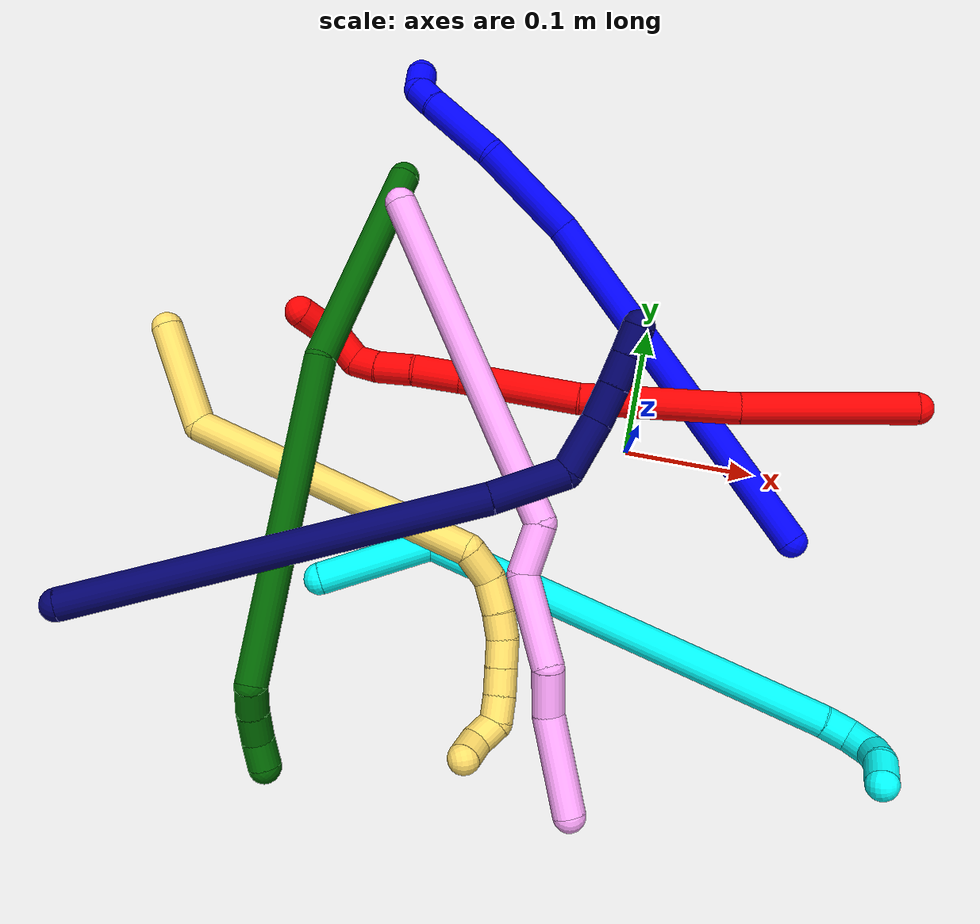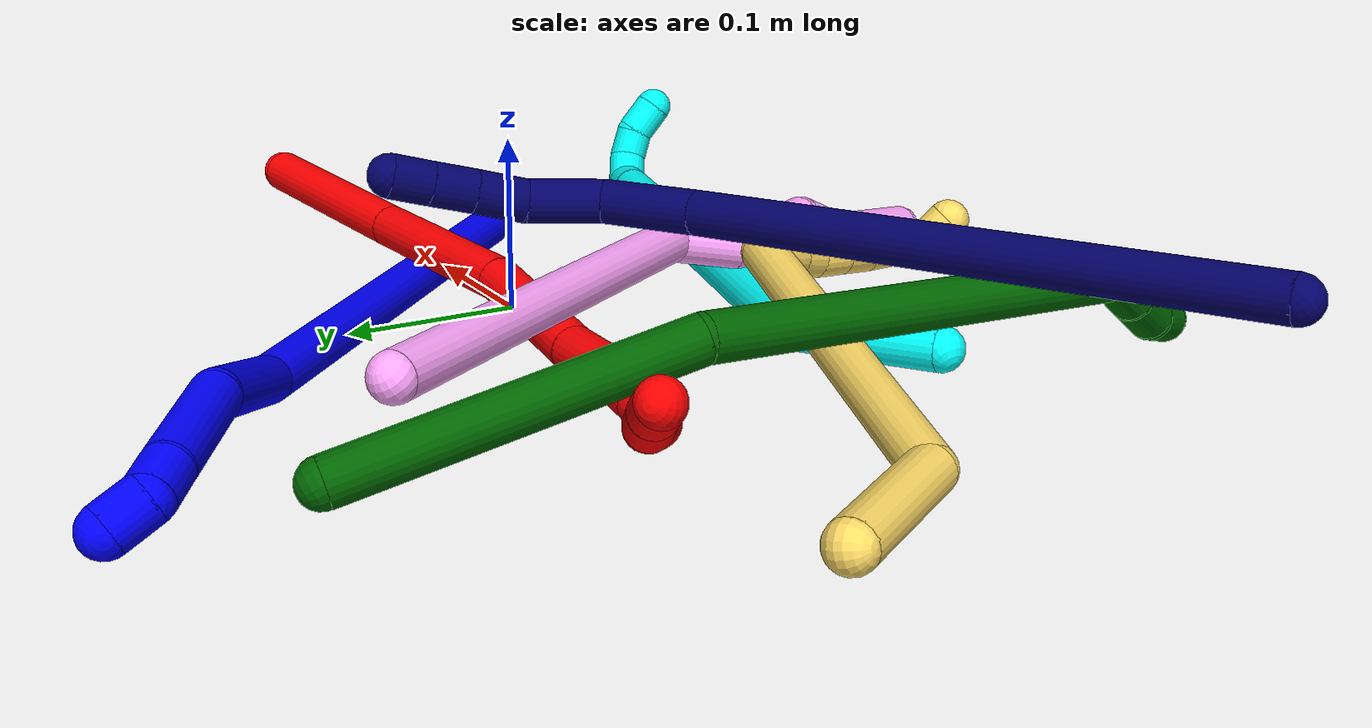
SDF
<sdf version="1.7">
 <world name="default">
  <plugin name="TubeGeneratorPlugin" filename="libtube_generator_plugin.so"/>
  <model name="photoneo_s_sensor">
   <static>1</static>
   <pose>0 0 2 1.57079 1.57079 3.14159</pose>
   <link name="link">
    <inertial><mass>0.1</mass></inertial>
    <sensor name="sensor" type="depth">
     <update_rate>30</update_rate>
     <camera>
      <horizontal_fov>1.22</horizontal_fov>
      <image><width>1920</width><height>1200</height><format>B8G8R8</format></image>
      <clip><near>0.1</near><far>4</far></clip>
      <depth_camera><output>points</output></depth_camera>
     </camera>
     <plugin name="camera_plugin" filename="libgazebo_ros_depth_camera.so">
      <baseline>0.2</baseline>
      <alwaysOn>1</alwaysOn>
      <updateRate>0.0</updateRate>
      <cameraName>camera_ir</cameraName>
      <imageTopicName>/camera/color/image_raw</imageTopicName>
      <cameraInfoTopicName>/camera/color/camera_info</cameraInfoTopicName>
      <depthImageTopicName>/camera/depth/image_raw</depthImageTopicName>
      <depthImageCameraInfoTopicName>/camera/depth/camera_info</depthImageCameraInfoTopicName>
      <pointCloudTopicName>/camera/depth/points</pointCloudTopicName>
      <frameName>fr_optical</frameName>
      <pointCloudCutoff>0.1</pointCloudCutoff>
      <pointCloudCutoffMax>2.0</pointCloudCutoffMax>
      <distortionK1>0</distortionK1>
      <distortionK2>0</distortionK2>
      <distortionK3>0</distortionK3>
      <distortionT1>0</distortionT1>
      <distortionT2>0</distortionT2>
      <CxPrime>0</CxPrime>
      <Cx>0</Cx>
      <Cy>0</Cy>
      <focalLength>0</focalLength>
      <hackBaseline>0</hackBaseline>
     </plugin>
    </sensor>
   </link>
  </model>
  <gravity>0 0 -9.8</gravity>
  <magnetic_field>6e-06 2.3e-05 -4.2e-05</magnetic_field>
  <atmosphere type="adiabatic"/>
  <physics name="default_physics" default="0" type="ode">
   <max_step_size>0.003</max_step_size>
   <real_time_factor>1</real_time_factor>
   <real_time_update_rate>1000</real_time_update_rate>
   <max_contacts>10000</max_contacts>
   <ode>
    <solver>
     <type>quick</type>
     <iters>100</iters>
     <sor>1.3</sor>
     <use_dynamic_moi_rescaling>0</use_dynamic_moi_rescaling>
    </solver>
    <constraints>
     <contact_max_correcting_vel>0</contact_max_correcting_vel>
     <contact_surface_layer>0.001</contact_surface_layer>
     <cfm>0</cfm>
     <erp>0.2</erp>
    </constraints>
   </ode>
  </physics>
  <scene><ambient>0.4 0.4 0.4 1</ambient><background>0.7 0.7 0.7 1</background><shadows>0</shadows></scene>
  <audio><device>default</device></audio>
  <spherical_coordinates>
   <surface_model>EARTH_WGS84</surface_model>
   <latitude_deg>0</latitude_deg>
   <longitude_deg>0</longitude_deg>
   <elevation>0</elevation>
   <heading_deg>0</heading_deg>
  </spherical_coordinates>
  <model name="bin">
   <static>1</static>
   <link name="bottom">
    <collision name="collision-bottom">
     <pose>0 0 -0.01 0 -0 0</pose>
     <geometry><box><size>0.8 0.6 0.02</size></box></geometry>
     <surface>
      <friction><ode><mu>100</mu><mu2>100</mu2></ode></friction>
      <contact><collide_bitmask>65535</collide_bitmask></contact>
     </surface>
    </collision>
   </link>
   <link name="west_wall">
    <collision name="collision-west_wall">
     <pose>-0.41 0 0.1 0 -0 0</pose>
     <geometry><box><size>0.02 0.6 0.2</size></box></geometry>
     <surface>
      <friction><ode><mu>100</mu><mu2>100</mu2></ode></friction>
      <contact><collide_bitmask>65535</collide_bitmask></contact>
     </surface>
    </collision>
   </link>
   <link name="east_wall">
    <collision name="collision-east_wall">
     <pose>0.41 0 0.1 0 -0 0</pose>
     <geometry><box><size>0.02 0.6 0.2</size></box></geometry>
     <surface>
      <friction><ode><mu>100</mu><mu2>100</mu2></ode></friction>
      <contact><collide_bitmask>65535</collide_bitmask></contact>
     </surface>
    </collision>
   </link>
   <link name="south_wall">
    <collision name="collision-south_wall">
     <pose>0 -0.31 0.1 0 -0 0</pose>
     <geometry><box><size>0.8 0.02 0.2</size></box></geometry>
     <surface>
      <friction><ode><mu>100</mu><mu2>100</mu2></ode></friction>
      <contact><collide_bitmask>65535</collide_bitmask></contact>
     </surface>
    </collision>
   </link>
   <link name="north_wall">
    <collision name="collision-north_wall">
     <pose>0 0.31 0.1 0 -0 0</pose>
     <geometry><box><size>0.8 0.02 0.2</size></box></geometry>
     <surface>
      <friction><ode><mu>100</mu><mu2>100</mu2></ode></friction>
      <contact><collide_bitmask>65535</collide_bitmask></contact>
     </surface>
    </collision>
   </link>
  </model>
  <model name="1">
   <static>0</static>
   <link name="1">
    <collision name="collision-cylinder-e_1_1_4">
     <pose>-0.056234 0.048711 0.135348 -0.345466 -0.372665 0.065759</pose>
     <geometry><cylinder><radius>0.0125</radius><length>0.308895</length></cylinder></geometry>
     <surface>
      <friction><ode><mu>1.16</mu><mu2>1.16</mu2><slip1>0</slip1><slip2>0</slip2></ode></friction>
      <contact><ode><kp>1e+06</kp><kd>1</kd><max_vel>0</max_vel><min_depth>0.001</min_depth></ode></contact>
     </surface>
    </collision>
    <visual name="visual-cylinder-e_1_1_4">
     <pose>-0.056234 0.048711 0.135348 -0.345466 -0.372665 0.065759</pose>
     <geometry><cylinder><radius>0.0125</radius><length>0.308895</length></cylinder></geometry>
     <material><ambient>0 0 1 1</ambient></material>
    </visual>
    <collision name="collision-cylinder-e_2_4_5">
     <pose>-0.113896 0.113341 0.310005 -0.384758 -0.033646 0.006554</pose>
     <geometry><cylinder><radius>0.0125</radius><length>0.084868</length></cylinder></geometry>
     <surface>
      <friction><ode><mu>1.16</mu><mu2>1.16</mu2><slip1>0</slip1><slip2>0</slip2></ode></friction>
      <contact><ode><kp>1e+06</kp><kd>1</kd><max_vel>0</max_vel><min_depth>0.001</min_depth></ode></contact>
     </surface>
    </collision>
    <visual name="visual-cylinder-e_2_4_5">
     <pose>-0.113896 0.113341 0.310005 -0.384758 -0.033646 0.006554</pose>
     <geometry><cylinder><radius>0.0125</radius><length>0.084868</length></cylinder></geometry>
     <material><ambient>0 0 1 1</ambient></material>
    </visual>
    <collision name="collision-cylinder-e_3_5_6">
     <pose>-0.125329 0.132647 0.379857 -0.110473 -0.314776 0.017549</pose>
     <geometry><cylinder><radius>0.0125</radius><length>0.064636</length></cylinder></geometry>
     <surface>
      <friction><ode><mu>1.16</mu><mu2>1.16</mu2><slip1>0</slip1><slip2>0</slip2></ode></friction>
      <contact><ode><kp>1e+06</kp><kd>1</kd><max_vel>0</max_vel><min_depth>0.001</min_depth></ode></contact>
     </surface>
    </collision>
    <visual name="visual-cylinder-e_3_5_6">
     <pose>-0.125329 0.132647 0.379857 -0.110473 -0.314776 0.017549</pose>
     <geometry><cylinder><radius>0.0125</radius><length>0.064636</length></cylinder></geometry>
     <material><ambient>0 0 1 1</ambient></material>
    </visual>
    <collision name="collision-cylinder-e_4_6_7">
     <pose>-0.139977 0.136561 0.419648 -0.056815 -0.464591 0.013444</pose>
     <geometry><cylinder><radius>0.0125</radius><length>0.020723</length></cylinder></geometry>
     <surface>
      <friction><ode><mu>1.16</mu><mu2>1.16</mu2><slip1>0</slip1><slip2>0</slip2></ode></friction>
      <contact><ode><kp>1e+06</kp><kd>1</kd><max_vel>0</max_vel><min_depth>0.001</min_depth></ode></contact>
     </surface>
    </collision>
    <visual name="visual-cylinder-e_4_6_7">
     <pose>-0.139977 0.136561 0.419648 -0.056815 -0.464591 0.013444</pose>
     <geometry><cylinder><radius>0.0125</radius><length>0.020723</length></cylinder></geometry>
     <material><ambient>0 0 1 1</ambient></material>
    </visual>
    <collision name="collision-cylinder-e_5_7_2">
     <pose>-0.154194 0.13921 0.432473 -0.535761 -1.1609 0.356196</pose>
     <geometry><cylinder><radius>0.0125</radius><length>0.020878</length></cylinder></geometry>
     <surface>
      <friction><ode><mu>1.16</mu><mu2>1.16</mu2><slip1>0</slip1><slip2>0</slip2></ode></friction>
      <contact><ode><kp>1e+06</kp><kd>1</kd><max_vel>0</max_vel><min_depth>0.001</min_depth></ode></contact>
     </surface>
    </collision>
    <visual name="visual-cylinder-e_5_7_2">
     <pose>-0.154194 0.13921 0.432473 -0.535761 -1.1609 0.356196</pose>
     <geometry><cylinder><radius>0.0125</radius><length>0.020878</length></cylinder></geometry>
     <material><ambient>0 0 1 1</ambient></material>
    </visual>
    <collision name="collision-sphere-2">
     <pose>-0.163768 0.141334 0.43605 0 -0 0</pose>
     <geometry><sphere><radius>0.0125</radius></sphere></geometry>
     <surface>
      <friction><ode><mu>1.16</mu><mu2>1.16</mu2><slip1>0</slip1><slip2>0</slip2></ode></friction>
      <contact><ode><kp>1e+06</kp><kd>1</kd><max_vel>0</max_vel><min_depth>0.001</min_depth></ode></contact>
     </surface>
    </collision>
    <visual name="visual-sphere-2">
     <pose>-0.163768 0.141334 0.43605 0 -0 0</pose>
     <geometry><sphere><radius>0.0125</radius></sphere></geometry>
     <material><ambient>0 0 1 1</ambient></material>
    </visual>
    <collision name="collision-sphere-7">
     <pose>-0.14462 0.137087 0.428896 0 -0 0</pose>
     <geometry><sphere><radius>0.0125</radius></sphere></geometry>
     <surface>
      <friction><ode><mu>1.16</mu><mu2>1.16</mu2><slip1>0</slip1><slip2>0</slip2></ode></friction>
      <contact><ode><kp>1e+06</kp><kd>1</kd><max_vel>0</max_vel><min_depth>0.001</min_depth></ode></contact>
     </surface>
    </collision>
    <visual name="visual-sphere-7">
     <pose>-0.14462 0.137087 0.428896 0 -0 0</pose>
     <geometry><sphere><radius>0.0125</radius></sphere></geometry>
     <material><ambient>0 0 1 1</ambient></material>
    </visual>
    <collision name="collision-sphere-6">
     <pose>-0.135335 0.136035 0.410399 0 -0 0</pose>
     <geometry><sphere><radius>0.0125</radius></sphere></geometry>
     <surface>
      <friction><ode><mu>1.16</mu><mu2>1.16</mu2><slip1>0</slip1><slip2>0</slip2></ode></friction>
      <contact><ode><kp>1e+06</kp><kd>1</kd><max_vel>0</max_vel><min_depth>0.001</min_depth></ode></contact>
     </surface>
    </collision>
    <visual name="visual-sphere-6">
     <pose>-0.135335 0.136035 0.410399 0 -0 0</pose>
     <geometry><sphere><radius>0.0125</radius></sphere></geometry>
     <material><ambient>0 0 1 1</ambient></material>
    </visual>
    <collision name="collision-sphere-5">
     <pose>-0.115323 0.129259 0.349314 0 -0 0</pose>
     <geometry><sphere><radius>0.0125</radius></sphere></geometry>
     <surface>
      <friction><ode><mu>1.16</mu><mu2>1.16</mu2><slip1>0</slip1><slip2>0</slip2></ode></friction>
      <contact><ode><kp>1e+06</kp><kd>1</kd><max_vel>0</max_vel><min_depth>0.001</min_depth></ode></contact>
     </surface>
    </collision>
    <visual name="visual-sphere-5">
     <pose>-0.115323 0.129259 0.349314 0 -0 0</pose>
     <geometry><sphere><radius>0.0125</radius></sphere></geometry>
     <material><ambient>0 0 1 1</ambient></material>
    </visual>
    <collision name="collision-sphere-1">
     <geometry><sphere><radius>0.0125</radius></sphere></geometry>
     <surface>
      <friction><ode><mu>1.16</mu><mu2>1.16</mu2><slip1>0</slip1><slip2>0</slip2></ode></friction>
      <contact><ode><kp>1e+06</kp><kd>1</kd><max_vel>0</max_vel><min_depth>0.001</min_depth></ode></contact>
     </surface>
    </collision>
    <visual name="visual-sphere-1">
     <geometry><sphere><radius>0.0125</radius></sphere></geometry>
     <material><ambient>0 0 1 1</ambient></material>
    </visual>
    <collision name="collision-sphere-4">
     <pose>-0.112468 0.097423 0.270695 0 -0 0</pose>
     <geometry><sphere><radius>0.0125</radius></sphere></geometry>
     <surface>
      <friction><ode><mu>1.16</mu><mu2>1.16</mu2><slip1>0</slip1><slip2>0</slip2></ode></friction>
      <contact><ode><kp>1e+06</kp><kd>1</kd><max_vel>0</max_vel><min_depth>0.001</min_depth></ode></contact>
     </surface>
    </collision>
    <visual name="visual-sphere-4">
     <pose>-0.112468 0.097423 0.270695 0 -0 0</pose>
     <geometry><sphere><radius>0.0125</radius></sphere></geometry>
     <material><ambient>0 0 1 1</ambient></material>
    </visual>
    <inertial>
     <pose>-0.082515 0.077952 0.220791 0 -0 0</pose>
     <mass>0.5</mass>
     <inertia>
      <ixx>0.002513</ixx>
      <ixy>0</ixy>
      <ixz>0</ixz>
      <iyy>0.002579</iyy>
      <iyz>0</iyz>
      <izz>0.000143</izz>
     </inertia>
    </inertial>
   </link>
   <pose>0.136359 -0.047686 0.011483 1.55686 -0.72823 -1.84409</pose>
  </model>
  <model name="2">
   <static>0</static>
   <link name="2">
    <collision name="collision-cylinder-e_1_1_4">
     <pose>-0.058885 -0.009412 -0.030707 2.84419 -1.07148 -2.64722</pose>
     <geometry><cylinder><radius>0.0125</radius><length>0.134149</length></cylinder></geometry>
     <surface>
      <friction><ode><mu>1.16</mu><mu2>1.16</mu2><slip1>0</slip1><slip2>0</slip2></ode></friction>
      <contact><ode><kp>1e+06</kp><kd>1</kd><max_vel>0</max_vel><min_depth>0.001</min_depth></ode></contact>
     </surface>
    </collision>
    <visual name="visual-cylinder-e_1_1_4">
     <pose>-0.058885 -0.009412 -0.030707 2.84419 -1.07148 -2.64722</pose>
     <geometry><cylinder><radius>0.0125</radius><length>0.134149</length></cylinder></geometry>
     <material><ambient>1 0 0 1</ambient></material>
    </visual>
    <collision name="collision-cylinder-e_2_4_5">
     <pose>-0.170441 -0.02563 -0.09318 2.9305 -1.01813 -2.76642</pose>
     <geometry><cylinder><radius>0.0125</radius><length>0.123768</length></cylinder></geometry>
     <surface>
      <friction><ode><mu>1.16</mu><mu2>1.16</mu2><slip1>0</slip1><slip2>0</slip2></ode></friction>
      <contact><ode><kp>1e+06</kp><kd>1</kd><max_vel>0</max_vel><min_depth>0.001</min_depth></ode></contact>
     </surface>
    </collision>
    <visual name="visual-cylinder-e_2_4_5">
     <pose>-0.170441 -0.02563 -0.09318 2.9305 -1.01813 -2.76642</pose>
     <geometry><cylinder><radius>0.0125</radius><length>0.123768</length></cylinder></geometry>
     <material><ambient>1 0 0 1</ambient></material>
    </visual>
    <collision name="collision-cylinder-e_3_5_6">
     <pose>-0.259402 -0.043561 -0.153088 2.76518 -0.875729 -2.36885</pose>
     <geometry><cylinder><radius>0.0125</radius><length>0.094504</length></cylinder></geometry>
     <surface>
      <friction><ode><mu>1.16</mu><mu2>1.16</mu2><slip1>0</slip1><slip2>0</slip2></ode></friction>
      <contact><ode><kp>1e+06</kp><kd>1</kd><max_vel>0</max_vel><min_depth>0.001</min_depth></ode></contact>
     </surface>
    </collision>
    <visual name="visual-cylinder-e_3_5_6">
     <pose>-0.259402 -0.043561 -0.153088 2.76518 -0.875729 -2.36885</pose>
     <geometry><cylinder><radius>0.0125</radius><length>0.094504</length></cylinder></geometry>
     <material><ambient>1 0 0 1</ambient></material>
    </visual>
    <collision name="collision-cylinder-e_4_6_7">
     <pose>-0.310656 -0.056954 -0.192487 2.94265 -0.916296 -2.74223</pose>
     <geometry><cylinder><radius>0.0125</radius><length>0.037723</length></cylinder></geometry>
     <surface>
      <friction><ode><mu>1.16</mu><mu2>1.16</mu2><slip1>0</slip1><slip2>0</slip2></ode></friction>
      <contact><ode><kp>1e+06</kp><kd>1</kd><max_vel>0</max_vel><min_depth>0.001</min_depth></ode></contact>
     </surface>
    </collision>
    <visual name="visual-cylinder-e_4_6_7">
     <pose>-0.310656 -0.056954 -0.192487 2.94265 -0.916296 -2.74223</pose>
     <geometry><cylinder><radius>0.0125</radius><length>0.037723</length></cylinder></geometry>
     <material><ambient>1 0 0 1</ambient></material>
    </visual>
    <collision name="collision-cylinder-e_5_7_8">
     <pose>-0.337462 -0.063564 -0.211406 2.62625 -0.931313 -2.17561</pose>
     <geometry><cylinder><radius>0.0125</radius><length>0.029516</length></cylinder></geometry>
     <surface>
      <friction><ode><mu>1.16</mu><mu2>1.16</mu2><slip1>0</slip1><slip2>0</slip2></ode></friction>
      <contact><ode><kp>1e+06</kp><kd>1</kd><max_vel>0</max_vel><min_depth>0.001</min_depth></ode></contact>
     </surface>
    </collision>
    <visual name="visual-cylinder-e_5_7_8">
     <pose>-0.337462 -0.063564 -0.211406 2.62625 -0.931313 -2.17561</pose>
     <geometry><cylinder><radius>0.0125</radius><length>0.029516</length></cylinder></geometry>
     <material><ambient>1 0 0 1</ambient></material>
    </visual>
    <collision name="collision-cylinder-e_6_8_9">
     <pose>-0.356172 -0.071293 -0.225538 2.65898 -0.754867 -2.03047</pose>
     <geometry><cylinder><radius>0.0125</radius><length>0.02005</length></cylinder></geometry>
     <surface>
      <friction><ode><mu>1.16</mu><mu2>1.16</mu2><slip1>0</slip1><slip2>0</slip2></ode></friction>
      <contact><ode><kp>1e+06</kp><kd>1</kd><max_vel>0</max_vel><min_depth>0.001</min_depth></ode></contact>
     </surface>
    </collision>
    <visual name="visual-cylinder-e_6_8_9">
     <pose>-0.356172 -0.071293 -0.225538 2.65898 -0.754867 -2.03047</pose>
     <geometry><cylinder><radius>0.0125</radius><length>0.02005</length></cylinder></geometry>
     <material><ambient>1 0 0 1</ambient></material>
    </visual>
    <collision name="collision-cylinder-e_7_9_10">
     <pose>-0.364898 -0.074189 -0.241862 -3.09159 -0.185948 2.61756</pose>
     <geometry><cylinder><radius>0.0125</radius><length>0.020085</length></cylinder></geometry>
     <surface>
      <friction><ode><mu>1.16</mu><mu2>1.16</mu2><slip1>0</slip1><slip2>0</slip2></ode></friction>
      <contact><ode><kp>1e+06</kp><kd>1</kd><max_vel>0</max_vel><min_depth>0.001</min_depth></ode></contact>
     </surface>
    </collision>
    <visual name="visual-cylinder-e_7_9_10">
     <pose>-0.364898 -0.074189 -0.241862 -3.09159 -0.185948 2.61756</pose>
     <geometry><cylinder><radius>0.0125</radius><length>0.020085</length></cylinder></geometry>
     <material><ambient>1 0 0 1</ambient></material>
    </visual>
    <collision name="collision-cylinder-e_8_10_11">
     <pose>-0.370361 -0.069299 -0.260005 -2.65382 -0.367067 1.28182</pose>
     <geometry><cylinder><radius>0.0125</radius><length>0.020098</length></cylinder></geometry>
     <surface>
      <friction><ode><mu>1.16</mu><mu2>1.16</mu2><slip1>0</slip1><slip2>0</slip2></ode></friction>
      <contact><ode><kp>1e+06</kp><kd>1</kd><max_vel>0</max_vel><min_depth>0.001</min_depth></ode></contact>
     </surface>
    </collision>
    <visual name="visual-cylinder-e_8_10_11">
     <pose>-0.370361 -0.069299 -0.260005 -2.65382 -0.367067 1.28182</pose>
     <geometry><cylinder><radius>0.0125</radius><length>0.020098</length></cylinder></geometry>
     <material><ambient>1 0 0 1</ambient></material>
    </visual>
    <collision name="collision-cylinder-e_9_11_2">
     <pose>-0.378185 -0.060889 -0.276487 -2.68608 -0.432896 1.51817</pose>
     <geometry><cylinder><radius>0.0125</radius><length>0.020108</length></cylinder></geometry>
     <surface>
      <friction><ode><mu>1.16</mu><mu2>1.16</mu2><slip1>0</slip1><slip2>0</slip2></ode></friction>
      <contact><ode><kp>1e+06</kp><kd>1</kd><max_vel>0</max_vel><min_depth>0.001</min_depth></ode></contact>
     </surface>
    </collision>
    <visual name="visual-cylinder-e_9_11_2">
     <pose>-0.378185 -0.060889 -0.276487 -2.68608 -0.432896 1.51817</pose>
     <geometry><cylinder><radius>0.0125</radius><length>0.020108</length></cylinder></geometry>
     <material><ambient>1 0 0 1</ambient></material>
    </visual>
    <collision name="collision-sphere-2">
     <pose>-0.382403 -0.056874 -0.284683 0 -0 0</pose>
     <geometry><sphere><radius>0.0125</radius></sphere></geometry>
     <surface>
      <friction><ode><mu>1.16</mu><mu2>1.16</mu2><slip1>0</slip1><slip2>0</slip2></ode></friction>
      <contact><ode><kp>1e+06</kp><kd>1</kd><max_vel>0</max_vel><min_depth>0.001</min_depth></ode></contact>
     </surface>
    </collision>
    <visual name="visual-sphere-2">
     <pose>-0.382403 -0.056874 -0.284683 0 -0 0</pose>
     <geometry><sphere><radius>0.0125</radius></sphere></geometry>
     <material><ambient>1 0 0 1</ambient></material>
    </visual>
    <collision name="collision-sphere-11">
     <pose>-0.373968 -0.064903 -0.268291 0 -0 0</pose>
     <geometry><sphere><radius>0.0125</radius></sphere></geometry>
     <surface>
      <friction><ode><mu>1.16</mu><mu2>1.16</mu2><slip1>0</slip1><slip2>0</slip2></ode></friction>
      <contact><ode><kp>1e+06</kp><kd>1</kd><max_vel>0</max_vel><min_depth>0.001</min_depth></ode></contact>
     </surface>
    </collision>
    <visual name="visual-sphere-11">
     <pose>-0.373968 -0.064903 -0.268291 0 -0 0</pose>
     <geometry><sphere><radius>0.0125</radius></sphere></geometry>
     <material><ambient>1 0 0 1</ambient></material>
    </visual>
    <collision name="collision-sphere-10">
     <pose>-0.366755 -0.073695 -0.25172 0 -0 0</pose>
     <geometry><sphere><radius>0.0125</radius></sphere></geometry>
     <surface>
      <friction><ode><mu>1.16</mu><mu2>1.16</mu2><slip1>0</slip1><slip2>0</slip2></ode></friction>
      <contact><ode><kp>1e+06</kp><kd>1</kd><max_vel>0</max_vel><min_depth>0.001</min_depth></ode></contact>
     </surface>
    </collision>
    <visual name="visual-sphere-10">
     <pose>-0.366755 -0.073695 -0.25172 0 -0 0</pose>
     <geometry><sphere><radius>0.0125</radius></sphere></geometry>
     <material><ambient>1 0 0 1</ambient></material>
    </visual>
    <collision name="collision-sphere-9">
     <pose>-0.363041 -0.074682 -0.232005 0 -0 0</pose>
     <geometry><sphere><radius>0.0125</radius></sphere></geometry>
     <surface>
      <friction><ode><mu>1.16</mu><mu2>1.16</mu2><slip1>0</slip1><slip2>0</slip2></ode></friction>
      <contact><ode><kp>1e+06</kp><kd>1</kd><max_vel>0</max_vel><min_depth>0.001</min_depth></ode></contact>
     </surface>
    </collision>
    <visual name="visual-sphere-9">
     <pose>-0.363041 -0.074682 -0.232005 0 -0 0</pose>
     <geometry><sphere><radius>0.0125</radius></sphere></geometry>
     <material><ambient>1 0 0 1</ambient></material>
    </visual>
    <collision name="collision-sphere-4">
     <pose>-0.11777 -0.018823 -0.061414 0 -0 0</pose>
     <geometry><sphere><radius>0.0125</radius></sphere></geometry>
     <surface>
      <friction><ode><mu>1.16</mu><mu2>1.16</mu2><slip1>0</slip1><slip2>0</slip2></ode></friction>
      <contact><ode><kp>1e+06</kp><kd>1</kd><max_vel>0</max_vel><min_depth>0.001</min_depth></ode></contact>
     </surface>
    </collision>
    <visual name="visual-sphere-4">
     <pose>-0.11777 -0.018823 -0.061414 0 -0 0</pose>
     <geometry><sphere><radius>0.0125</radius></sphere></geometry>
     <material><ambient>1 0 0 1</ambient></material>
    </visual>
    <collision name="collision-sphere-1">
     <geometry><sphere><radius>0.0125</radius></sphere></geometry>
     <surface>
      <friction><ode><mu>1.16</mu><mu2>1.16</mu2><slip1>0</slip1><slip2>0</slip2></ode></friction>
      <contact><ode><kp>1e+06</kp><kd>1</kd><max_vel>0</max_vel><min_depth>0.001</min_depth></ode></contact>
     </surface>
    </collision>
    <visual name="visual-sphere-1">
     <geometry><sphere><radius>0.0125</radius></sphere></geometry>
     <material><ambient>1 0 0 1</ambient></material>
    </visual>
    <collision name="collision-sphere-8">
     <pose>-0.349303 -0.067904 -0.21907 0 -0 0</pose>
     <geometry><sphere><radius>0.0125</radius></sphere></geometry>
     <surface>
      <friction><ode><mu>1.16</mu><mu2>1.16</mu2><slip1>0</slip1><slip2>0</slip2></ode></friction>
      <contact><ode><kp>1e+06</kp><kd>1</kd><max_vel>0</max_vel><min_depth>0.001</min_depth></ode></contact>
     </surface>
    </collision>
    <visual name="visual-sphere-8">
     <pose>-0.349303 -0.067904 -0.21907 0 -0 0</pose>
     <geometry><sphere><radius>0.0125</radius></sphere></geometry>
     <material><ambient>1 0 0 1</ambient></material>
    </visual>
    <collision name="collision-sphere-5">
     <pose>-0.223112 -0.032437 -0.124945 0 -0 0</pose>
     <geometry><sphere><radius>0.0125</radius></sphere></geometry>
     <surface>
      <friction><ode><mu>1.16</mu><mu2>1.16</mu2><slip1>0</slip1><slip2>0</slip2></ode></friction>
      <contact><ode><kp>1e+06</kp><kd>1</kd><max_vel>0</max_vel><min_depth>0.001</min_depth></ode></contact>
     </surface>
    </collision>
    <visual name="visual-sphere-5">
     <pose>-0.223112 -0.032437 -0.124945 0 -0 0</pose>
     <geometry><sphere><radius>0.0125</radius></sphere></geometry>
     <material><ambient>1 0 0 1</ambient></material>
    </visual>
    <collision name="collision-sphere-6">
     <pose>-0.295692 -0.054685 -0.181232 0 -0 0</pose>
     <geometry><sphere><radius>0.0125</radius></sphere></geometry>
     <surface>
      <friction><ode><mu>1.16</mu><mu2>1.16</mu2><slip1>0</slip1><slip2>0</slip2></ode></friction>
      <contact><ode><kp>1e+06</kp><kd>1</kd><max_vel>0</max_vel><min_depth>0.001</min_depth></ode></contact>
     </surface>
    </collision>
    <visual name="visual-sphere-6">
     <pose>-0.295692 -0.054685 -0.181232 0 -0 0</pose>
     <geometry><sphere><radius>0.0125</radius></sphere></geometry>
     <material><ambient>1 0 0 1</ambient></material>
    </visual>
    <collision name="collision-sphere-7">
     <pose>-0.32562 -0.059223 -0.203743 0 -0 0</pose>
     <geometry><sphere><radius>0.0125</radius></sphere></geometry>
     <surface>
      <friction><ode><mu>1.16</mu><mu2>1.16</mu2><slip1>0</slip1><slip2>0</slip2></ode></friction>
      <contact><ode><kp>1e+06</kp><kd>1</kd><max_vel>0</max_vel><min_depth>0.001</min_depth></ode></contact>
     </surface>
    </collision>
    <visual name="visual-sphere-7">
     <pose>-0.32562 -0.059223 -0.203743 0 -0 0</pose>
     <geometry><sphere><radius>0.0125</radius></sphere></geometry>
     <material><ambient>1 0 0 1</ambient></material>
    </visual>
    <inertial>
     <pose>-0.209413 -0.036225 -0.127571 0 -0 0</pose>
     <mass>0.5</mass>
     <inertia>
      <ixx>-0.000348</ixx>
      <ixy>0</ixy>
      <ixz>0</ixz>
      <iyy>0.000316</iyy>
      <iyz>0</iyz>
      <izz>0.000429</izz>
     </inertia>
    </inertial>
   </link>
   <pose>0.209856 0.065719 0.045869 1.82352 -0.055391 0.673165</pose>
  </model>
  <model name="3">
   <static>0</static>
   <link name="3">
    <collision name="collision-cylinder-e_1_1_4">
     <pose>0.007689 -0.031935 -0.03007 2.32613 0.173532 0.397446</pose>
     <geometry><cylinder><radius>0.0125</radius><length>0.089067</length></cylinder></geometry>
     <surface>
      <friction><ode><mu>1.16</mu><mu2>1.16</mu2><slip1>0</slip1><slip2>0</slip2></ode></friction>
      <contact><ode><kp>1e+06</kp><kd>1</kd><max_vel>0</max_vel><min_depth>0.001</min_depth></ode></contact>
     </surface>
    </collision>
    <visual name="visual-cylinder-e_1_1_4">
     <pose>0.007689 -0.031935 -0.03007 2.32613 0.173532 0.397446</pose>
     <geometry><cylinder><radius>0.0125</radius><length>0.089067</length></cylinder></geometry>
     <material><ambient>0.003922 1 0.996078 1</ambient></material>
    </visual>
    <collision name="collision-cylinder-e_2_4_5">
     <pose>0.112898 -0.088301 -0.186795 2.95105 0.647348 2.58657</pose>
     <geometry><cylinder><radius>0.0125</radius><length>0.323408</length></cylinder></geometry>
     <surface>
      <friction><ode><mu>1.16</mu><mu2>1.16</mu2><slip1>0</slip1><slip2>0</slip2></ode></friction>
      <contact><ode><kp>1e+06</kp><kd>1</kd><max_vel>0</max_vel><min_depth>0.001</min_depth></ode></contact>
     </surface>
    </collision>
    <visual name="visual-cylinder-e_2_4_5">
     <pose>0.112898 -0.088301 -0.186795 2.95105 0.647348 2.58657</pose>
     <geometry><cylinder><radius>0.0125</radius><length>0.323408</length></cylinder></geometry>
     <material><ambient>0.003922 1 0.996078 1</ambient></material>
    </visual>
    <collision name="collision-cylinder-e_3_5_6">
     <pose>0.218166 -0.114174 -0.32156 2.96555 0.754846 2.70352</pose>
     <geometry><cylinder><radius>0.0125</radius><length>0.02262</length></cylinder></geometry>
     <surface>
      <friction><ode><mu>1.16</mu><mu2>1.16</mu2><slip1>0</slip1><slip2>0</slip2></ode></friction>
      <contact><ode><kp>1e+06</kp><kd>1</kd><max_vel>0</max_vel><min_depth>0.001</min_depth></ode></contact>
     </surface>
    </collision>
    <visual name="visual-cylinder-e_3_5_6">
     <pose>0.218166 -0.114174 -0.32156 2.96555 0.754846 2.70352</pose>
     <geometry><cylinder><radius>0.0125</radius><length>0.02262</length></cylinder></geometry>
     <material><ambient>0.003922 1 0.996078 1</ambient></material>
    </visual>
    <collision name="collision-cylinder-e_4_6_7">
     <pose>0.227655 -0.11156 -0.339678 -2.75651 0.159686 -0.778902</pose>
     <geometry><cylinder><radius>0.0125</radius><length>0.021874</length></cylinder></geometry>
     <surface>
      <friction><ode><mu>1.16</mu><mu2>1.16</mu2><slip1>0</slip1><slip2>0</slip2></ode></friction>
      <contact><ode><kp>1e+06</kp><kd>1</kd><max_vel>0</max_vel><min_depth>0.001</min_depth></ode></contact>
     </surface>
    </collision>
    <visual name="visual-cylinder-e_4_6_7">
     <pose>0.227655 -0.11156 -0.339678 -2.75651 0.159686 -0.778902</pose>
     <geometry><cylinder><radius>0.0125</radius><length>0.021874</length></cylinder></geometry>
     <material><ambient>0.003922 1 0.996078 1</ambient></material>
    </visual>
    <collision name="collision-cylinder-e_5_7_8">
     <pose>0.225791 -0.100528 -0.35603 -2.30889 -0.364843 0.79043</pose>
     <geometry><cylinder><radius>0.0125</radius><length>0.020191</length></cylinder></geometry>
     <surface>
      <friction><ode><mu>1.16</mu><mu2>1.16</mu2><slip1>0</slip1><slip2>0</slip2></ode></friction>
      <contact><ode><kp>1e+06</kp><kd>1</kd><max_vel>0</max_vel><min_depth>0.001</min_depth></ode></contact>
     </surface>
    </collision>
    <visual name="visual-cylinder-e_5_7_8">
     <pose>0.225791 -0.100528 -0.35603 -2.30889 -0.364843 0.79043</pose>
     <geometry><cylinder><radius>0.0125</radius><length>0.020191</length></cylinder></geometry>
     <material><ambient>0.003922 1 0.996078 1</ambient></material>
    </visual>
    <collision name="collision-cylinder-e_6_8_2">
     <pose>0.220301 -0.083241 -0.366911 -1.98512 -0.166092 0.253704</pose>
     <geometry><cylinder><radius>0.0125</radius><length>0.022841</length></cylinder></geometry>
     <surface>
      <friction><ode><mu>1.16</mu><mu2>1.16</mu2><slip1>0</slip1><slip2>0</slip2></ode></friction>
      <contact><ode><kp>1e+06</kp><kd>1</kd><max_vel>0</max_vel><min_depth>0.001</min_depth></ode></contact>
     </surface>
    </collision>
    <visual name="visual-cylinder-e_6_8_2">
     <pose>0.220301 -0.083241 -0.366911 -1.98512 -0.166092 0.253704</pose>
     <geometry><cylinder><radius>0.0125</radius><length>0.022841</length></cylinder></geometry>
     <material><ambient>0.003922 1 0.996078 1</ambient></material>
    </visual>
    <collision name="collision-sphere-2">
     <pose>0.218413 -0.07293 -0.371445 0 -0 0</pose>
     <geometry><sphere><radius>0.0125</radius></sphere></geometry>
     <surface>
      <friction><ode><mu>1.16</mu><mu2>1.16</mu2><slip1>0</slip1><slip2>0</slip2></ode></friction>
      <contact><ode><kp>1e+06</kp><kd>1</kd><max_vel>0</max_vel><min_depth>0.001</min_depth></ode></contact>
     </surface>
    </collision>
    <visual name="visual-sphere-2">
     <pose>0.218413 -0.07293 -0.371445 0 -0 0</pose>
     <geometry><sphere><radius>0.0125</radius></sphere></geometry>
     <material><ambient>0.003922 1 0.996078 1</ambient></material>
    </visual>
    <collision name="collision-sphere-4">
     <pose>0.015378 -0.063871 -0.060141 0 -0 0</pose>
     <geometry><sphere><radius>0.0125</radius></sphere></geometry>
     <surface>
      <friction><ode><mu>1.16</mu><mu2>1.16</mu2><slip1>0</slip1><slip2>0</slip2></ode></friction>
      <contact><ode><kp>1e+06</kp><kd>1</kd><max_vel>0</max_vel><min_depth>0.001</min_depth></ode></contact>
     </surface>
    </collision>
    <visual name="visual-sphere-4">
     <pose>0.015378 -0.063871 -0.060141 0 -0 0</pose>
     <geometry><sphere><radius>0.0125</radius></sphere></geometry>
     <material><ambient>0.003922 1 0.996078 1</ambient></material>
    </visual>
    <collision name="collision-sphere-1">
     <geometry><sphere><radius>0.0125</radius></sphere></geometry>
     <surface>
      <friction><ode><mu>1.16</mu><mu2>1.16</mu2><slip1>0</slip1><slip2>0</slip2></ode></friction>
      <contact><ode><kp>1e+06</kp><kd>1</kd><max_vel>0</max_vel><min_depth>0.001</min_depth></ode></contact>
     </surface>
    </collision>
    <visual name="visual-sphere-1">
     <geometry><sphere><radius>0.0125</radius></sphere></geometry>
     <material><ambient>0.003922 1 0.996078 1</ambient></material>
    </visual>
    <collision name="collision-sphere-8">
     <pose>0.222189 -0.093551 -0.362376 0 -0 0</pose>
     <geometry><sphere><radius>0.0125</radius></sphere></geometry>
     <surface>
      <friction><ode><mu>1.16</mu><mu2>1.16</mu2><slip1>0</slip1><slip2>0</slip2></ode></friction>
      <contact><ode><kp>1e+06</kp><kd>1</kd><max_vel>0</max_vel><min_depth>0.001</min_depth></ode></contact>
     </surface>
    </collision>
    <visual name="visual-sphere-8">
     <pose>0.222189 -0.093551 -0.362376 0 -0 0</pose>
     <geometry><sphere><radius>0.0125</radius></sphere></geometry>
     <material><ambient>0.003922 1 0.996078 1</ambient></material>
    </visual>
    <collision name="collision-sphere-5">
     <pose>0.210417 -0.112731 -0.313449 0 -0 0</pose>
     <geometry><sphere><radius>0.0125</radius></sphere></geometry>
     <surface>
      <friction><ode><mu>1.16</mu><mu2>1.16</mu2><slip1>0</slip1><slip2>0</slip2></ode></friction>
      <contact><ode><kp>1e+06</kp><kd>1</kd><max_vel>0</max_vel><min_depth>0.001</min_depth></ode></contact>
     </surface>
    </collision>
    <visual name="visual-sphere-5">
     <pose>0.210417 -0.112731 -0.313449 0 -0 0</pose>
     <geometry><sphere><radius>0.0125</radius></sphere></geometry>
     <material><ambient>0.003922 1 0.996078 1</ambient></material>
    </visual>
    <collision name="collision-sphere-6">
     <pose>0.225916 -0.115616 -0.329671 0 -0 0</pose>
     <geometry><sphere><radius>0.0125</radius></sphere></geometry>
     <surface>
      <friction><ode><mu>1.16</mu><mu2>1.16</mu2><slip1>0</slip1><slip2>0</slip2></ode></friction>
      <contact><ode><kp>1e+06</kp><kd>1</kd><max_vel>0</max_vel><min_depth>0.001</min_depth></ode></contact>
     </surface>
    </collision>
    <visual name="visual-sphere-6">
     <pose>0.225916 -0.115616 -0.329671 0 -0 0</pose>
     <geometry><sphere><radius>0.0125</radius></sphere></geometry>
     <material><ambient>0.003922 1 0.996078 1</ambient></material>
    </visual>
    <collision name="collision-sphere-7">
     <pose>0.229394 -0.107504 -0.349685 0 -0 0</pose>
     <geometry><sphere><radius>0.0125</radius></sphere></geometry>
     <surface>
      <friction><ode><mu>1.16</mu><mu2>1.16</mu2><slip1>0</slip1><slip2>0</slip2></ode></friction>
      <contact><ode><kp>1e+06</kp><kd>1</kd><max_vel>0</max_vel><min_depth>0.001</min_depth></ode></contact>
     </surface>
    </collision>
    <visual name="visual-sphere-7">
     <pose>0.229394 -0.107504 -0.349685 0 -0 0</pose>
     <geometry><sphere><radius>0.0125</radius></sphere></geometry>
     <material><ambient>0.003922 1 0.996078 1</ambient></material>
    </visual>
    <inertial>
     <pose>0.113404 -0.080711 -0.186724 0 -0 0</pose>
     <mass>0.5</mass>
     <inertia>
      <ixx>-0.000628</ixx>
      <ixy>0</ixy>
      <ixz>0</ixz>
      <iyy>0.003706</iyy>
      <iyz>0</iyz>
      <izz>-0.001279</izz>
     </inertia>
    </inertial>
   </link>
   <pose>-0.214287 -0.144157 0.01554 2.47558 0.707245 -0.883482</pose>
  </model>
  <model name="4">
   <static>0</static>
   <link name="4">
    <collision name="collision-cylinder-e_1_1_4">
     <pose>0.013494 -0.112571 0.078038 0.964625 0.098198 0.051442</pose>
     <geometry><cylinder><radius>0.0125</radius><length>0.275277</length></cylinder></geometry>
     <surface>
      <friction><ode><mu>1.16</mu><mu2>1.16</mu2><slip1>0</slip1><slip2>0</slip2></ode></friction>
      <contact><ode><kp>1e+06</kp><kd>1</kd><max_vel>0</max_vel><min_depth>0.001</min_depth></ode></contact>
     </surface>
    </collision>
    <visual name="visual-cylinder-e_1_1_4">
     <pose>0.013494 -0.112571 0.078038 0.964625 0.098198 0.051442</pose>
     <geometry><cylinder><radius>0.0125</radius><length>0.275277</length></cylinder></geometry>
     <material><ambient>1 0.65098 0.996078 1</ambient></material>
    </visual>
    <collision name="collision-cylinder-e_2_4_5">
     <pose>0.039606 -0.231407 0.17072 0.404263 0.669991 0.142438</pose>
     <geometry><cylinder><radius>0.0125</radius><length>0.040639</length></cylinder></geometry>
     <surface>
      <friction><ode><mu>1.16</mu><mu2>1.16</mu2><slip1>0</slip1><slip2>0</slip2></ode></friction>
      <contact><ode><kp>1e+06</kp><kd>1</kd><max_vel>0</max_vel><min_depth>0.001</min_depth></ode></contact>
     </surface>
    </collision>
    <visual name="visual-cylinder-e_2_4_5">
     <pose>0.039606 -0.231407 0.17072 0.404263 0.669991 0.142438</pose>
     <geometry><cylinder><radius>0.0125</radius><length>0.040639</length></cylinder></geometry>
     <material><ambient>1 0.65098 0.996078 1</ambient></material>
    </visual>
    <collision name="collision-cylinder-e_3_5_6">
     <pose>0.061351 -0.26613 0.204997 0.966848 0.2581 0.136042</pose>
     <geometry><cylinder><radius>0.0125</radius><length>0.071516</length></cylinder></geometry>
     <surface>
      <friction><ode><mu>1.16</mu><mu2>1.16</mu2><slip1>0</slip1><slip2>0</slip2></ode></friction>
      <contact><ode><kp>1e+06</kp><kd>1</kd><max_vel>0</max_vel><min_depth>0.001</min_depth></ode></contact>
     </surface>
    </collision>
    <visual name="visual-cylinder-e_3_5_6">
     <pose>0.061351 -0.26613 0.204997 0.966848 0.2581 0.136042</pose>
     <geometry><cylinder><radius>0.0125</radius><length>0.071516</length></cylinder></geometry>
     <material><ambient>1 0.65098 0.996078 1</ambient></material>
    </visual>
    <collision name="collision-cylinder-e_4_6_7">
     <pose>0.074917 -0.301443 0.240855 0.399793 0.246848 0.050257</pose>
     <geometry><cylinder><radius>0.0125</radius><length>0.036326</length></cylinder></geometry>
     <surface>
      <friction><ode><mu>1.16</mu><mu2>1.16</mu2><slip1>0</slip1><slip2>0</slip2></ode></friction>
      <contact><ode><kp>1e+06</kp><kd>1</kd><max_vel>0</max_vel><min_depth>0.001</min_depth></ode></contact>
     </surface>
    </collision>
    <visual name="visual-cylinder-e_4_6_7">
     <pose>0.074917 -0.301443 0.240855 0.399793 0.246848 0.050257</pose>
     <geometry><cylinder><radius>0.0125</radius><length>0.036326</length></cylinder></geometry>
     <material><ambient>1 0.65098 0.996078 1</ambient></material>
    </visual>
    <collision name="collision-cylinder-e_5_7_2">
     <pose>0.088327 -0.334227 0.283543 0.7752 0.237593 0.09738</pose>
     <geometry><cylinder><radius>0.0125</radius><length>0.076242</length></cylinder></geometry>
     <surface>
      <friction><ode><mu>1.16</mu><mu2>1.16</mu2><slip1>0</slip1><slip2>0</slip2></ode></friction>
      <contact><ode><kp>1e+06</kp><kd>1</kd><max_vel>0</max_vel><min_depth>0.001</min_depth></ode></contact>
     </surface>
    </collision>
    <visual name="visual-cylinder-e_5_7_2">
     <pose>0.088327 -0.334227 0.283543 0.7752 0.237593 0.09738</pose>
     <geometry><cylinder><radius>0.0125</radius><length>0.076242</length></cylinder></geometry>
     <material><ambient>1 0.65098 0.996078 1</ambient></material>
    </visual>
    <collision name="collision-sphere-2">
     <pose>0.097299 -0.360157 0.310007 0 -0 0</pose>
     <geometry><sphere><radius>0.0125</radius></sphere></geometry>
     <surface>
      <friction><ode><mu>1.16</mu><mu2>1.16</mu2><slip1>0</slip1><slip2>0</slip2></ode></friction>
      <contact><ode><kp>1e+06</kp><kd>1</kd><max_vel>0</max_vel><min_depth>0.001</min_depth></ode></contact>
     </surface>
    </collision>
    <visual name="visual-sphere-2">
     <pose>0.097299 -0.360157 0.310007 0 -0 0</pose>
     <geometry><sphere><radius>0.0125</radius></sphere></geometry>
     <material><ambient>1 0.65098 0.996078 1</ambient></material>
    </visual>
    <collision name="collision-sphere-7">
     <pose>0.079355 -0.308298 0.257079 0 -0 0</pose>
     <geometry><sphere><radius>0.0125</radius></sphere></geometry>
     <surface>
      <friction><ode><mu>1.16</mu><mu2>1.16</mu2><slip1>0</slip1><slip2>0</slip2></ode></friction>
      <contact><ode><kp>1e+06</kp><kd>1</kd><max_vel>0</max_vel><min_depth>0.001</min_depth></ode></contact>
     </surface>
    </collision>
    <visual name="visual-sphere-7">
     <pose>0.079355 -0.308298 0.257079 0 -0 0</pose>
     <geometry><sphere><radius>0.0125</radius></sphere></geometry>
     <material><ambient>1 0.65098 0.996078 1</ambient></material>
    </visual>
    <collision name="collision-sphere-6">
     <pose>0.070478 -0.294587 0.224632 0 -0 0</pose>
     <geometry><sphere><radius>0.0125</radius></sphere></geometry>
     <surface>
      <friction><ode><mu>1.16</mu><mu2>1.16</mu2><slip1>0</slip1><slip2>0</slip2></ode></friction>
      <contact><ode><kp>1e+06</kp><kd>1</kd><max_vel>0</max_vel><min_depth>0.001</min_depth></ode></contact>
     </surface>
    </collision>
    <visual name="visual-sphere-6">
     <pose>0.070478 -0.294587 0.224632 0 -0 0</pose>
     <geometry><sphere><radius>0.0125</radius></sphere></geometry>
     <material><ambient>1 0.65098 0.996078 1</ambient></material>
    </visual>
    <collision name="collision-sphere-5">
     <pose>0.052224 -0.237672 0.185363 0 -0 0</pose>
     <geometry><sphere><radius>0.0125</radius></sphere></geometry>
     <surface>
      <friction><ode><mu>1.16</mu><mu2>1.16</mu2><slip1>0</slip1><slip2>0</slip2></ode></friction>
      <contact><ode><kp>1e+06</kp><kd>1</kd><max_vel>0</max_vel><min_depth>0.001</min_depth></ode></contact>
     </surface>
    </collision>
    <visual name="visual-sphere-5">
     <pose>0.052224 -0.237672 0.185363 0 -0 0</pose>
     <geometry><sphere><radius>0.0125</radius></sphere></geometry>
     <material><ambient>1 0.65098 0.996078 1</ambient></material>
    </visual>
    <collision name="collision-sphere-1">
     <geometry><sphere><radius>0.0125</radius></sphere></geometry>
     <surface>
      <friction><ode><mu>1.16</mu><mu2>1.16</mu2><slip1>0</slip1><slip2>0</slip2></ode></friction>
      <contact><ode><kp>1e+06</kp><kd>1</kd><max_vel>0</max_vel><min_depth>0.001</min_depth></ode></contact>
     </surface>
    </collision>
    <visual name="visual-sphere-1">
     <geometry><sphere><radius>0.0125</radius></sphere></geometry>
     <material><ambient>1 0.65098 0.996078 1</ambient></material>
    </visual>
    <collision name="collision-sphere-4">
     <pose>0.026988 -0.225142 0.156077 0 -0 0</pose>
     <geometry><sphere><radius>0.0125</radius></sphere></geometry>
     <surface>
      <friction><ode><mu>1.16</mu><mu2>1.16</mu2><slip1>0</slip1><slip2>0</slip2></ode></friction>
      <contact><ode><kp>1e+06</kp><kd>1</kd><max_vel>0</max_vel><min_depth>0.001</min_depth></ode></contact>
     </surface>
    </collision>
    <visual name="visual-sphere-4">
     <pose>0.026988 -0.225142 0.156077 0 -0 0</pose>
     <geometry><sphere><radius>0.0125</radius></sphere></geometry>
     <material><ambient>1 0.65098 0.996078 1</ambient></material>
    </visual>
    <inertial>
     <pose>0.038335 -0.191715 0.146895 0 -0 0</pose>
     <mass>0.5</mass>
     <inertia>
      <ixx>0.001926</ixx>
      <ixy>0</ixy>
      <ixz>0</ixz>
      <iyy>0.001133</iyy>
      <iyz>0</iyz>
      <izz>0.001317</izz>
     </inertia>
    </inertial>
   </link>
   <pose>-0.210376 0.152727 0.051235 -2.60076 -0.377363 -2.43121</pose>
  </model>
  <model name="5">
   <static>0</static>
   <link name="5">
    <collision name="collision-cylinder-e_1_1_4">
     <pose>0.031659 -0.028203 -0.006794 1.80721 0.829047 1.01887</pose>
     <geometry><cylinder><radius>0.0125</radius><length>0.085881</length></cylinder></geometry>
     <surface>
      <friction><ode><mu>1.16</mu><mu2>1.16</mu2><slip1>0</slip1><slip2>0</slip2></ode></friction>
      <contact><ode><kp>1e+06</kp><kd>1</kd><max_vel>0</max_vel><min_depth>0.001</min_depth></ode></contact>
     </surface>
    </collision>
    <visual name="visual-cylinder-e_1_1_4">
     <pose>0.031659 -0.028203 -0.006794 1.80721 0.829047 1.01887</pose>
     <geometry><cylinder><radius>0.0125</radius><length>0.085881</length></cylinder></geometry>
     <material><ambient>1 0.858824 0.4 1</ambient></material>
    </visual>
    <collision name="collision-cylinder-e_2_4_5">
     <pose>0.139608 -0.079029 -0.102065 2.89126 0.695947 2.4738</pose>
     <geometry><cylinder><radius>0.0125</radius><length>0.23799</length></cylinder></geometry>
     <surface>
      <friction><ode><mu>1.16</mu><mu2>1.16</mu2><slip1>0</slip1><slip2>0</slip2></ode></friction>
      <contact><ode><kp>1e+06</kp><kd>1</kd><max_vel>0</max_vel><min_depth>0.001</min_depth></ode></contact>
     </surface>
    </collision>
    <visual name="visual-cylinder-e_2_4_5">
     <pose>0.139608 -0.079029 -0.102065 2.89126 0.695947 2.4738</pose>
     <geometry><cylinder><radius>0.0125</radius><length>0.23799</length></cylinder></geometry>
     <material><ambient>1 0.858824 0.4 1</ambient></material>
    </visual>
    <collision name="collision-cylinder-e_3_5_6">
     <pose>0.221064 -0.112373 -0.197268 2.13117 0.387562 0.681914</pose>
     <geometry><cylinder><radius>0.0125</radius><length>0.027341</length></cylinder></geometry>
     <surface>
      <friction><ode><mu>1.16</mu><mu2>1.16</mu2><slip1>0</slip1><slip2>0</slip2></ode></friction>
      <contact><ode><kp>1e+06</kp><kd>1</kd><max_vel>0</max_vel><min_depth>0.001</min_depth></ode></contact>
     </surface>
    </collision>
    <visual name="visual-cylinder-e_3_5_6">
     <pose>0.221064 -0.112373 -0.197268 2.13117 0.387562 0.681914</pose>
     <geometry><cylinder><radius>0.0125</radius><length>0.027341</length></cylinder></geometry>
     <material><ambient>1 0.858824 0.4 1</ambient></material>
    </visual>
    <collision name="collision-cylinder-e_4_6_7">
     <pose>0.234071 -0.133459 -0.205429 1.70827 0.643072 0.730399</pose>
     <geometry><cylinder><radius>0.0125</radius><length>0.026151</length></cylinder></geometry>
     <surface>
      <friction><ode><mu>1.16</mu><mu2>1.16</mu2><slip1>0</slip1><slip2>0</slip2></ode></friction>
      <contact><ode><kp>1e+06</kp><kd>1</kd><max_vel>0</max_vel><min_depth>0.001</min_depth></ode></contact>
     </surface>
    </collision>
    <visual name="visual-cylinder-e_4_6_7">
     <pose>0.234071 -0.133459 -0.205429 1.70827 0.643072 0.730399</pose>
     <geometry><cylinder><radius>0.0125</radius><length>0.026151</length></cylinder></geometry>
     <material><ambient>1 0.858824 0.4 1</ambient></material>
    </visual>
    <collision name="collision-cylinder-e_5_7_8">
     <pose>0.247444 -0.152476 -0.20705 1.59245 0.568774 0.580546</pose>
     <geometry><cylinder><radius>0.0125</radius><length>0.020542</length></cylinder></geometry>
     <surface>
      <friction><ode><mu>1.16</mu><mu2>1.16</mu2><slip1>0</slip1><slip2>0</slip2></ode></friction>
      <contact><ode><kp>1e+06</kp><kd>1</kd><max_vel>0</max_vel><min_depth>0.001</min_depth></ode></contact>
     </surface>
    </collision>
    <visual name="visual-cylinder-e_5_7_8">
     <pose>0.247444 -0.152476 -0.20705 1.59245 0.568774 0.580546</pose>
     <geometry><cylinder><radius>0.0125</radius><length>0.020542</length></cylinder></geometry>
     <material><ambient>1 0.858824 0.4 1</ambient></material>
    </visual>
    <collision name="collision-cylinder-e_6_8_9">
     <pose>0.259383 -0.169385 -0.204881 1.29278 0.641032 0.490846</pose>
     <geometry><cylinder><radius>0.0125</radius><length>0.021427</length></cylinder></geometry>
     <surface>
      <friction><ode><mu>1.16</mu><mu2>1.16</mu2><slip1>0</slip1><slip2>0</slip2></ode></friction>
      <contact><ode><kp>1e+06</kp><kd>1</kd><max_vel>0</max_vel><min_depth>0.001</min_depth></ode></contact>
     </surface>
    </collision>
    <visual name="visual-cylinder-e_6_8_9">
     <pose>0.259383 -0.169385 -0.204881 1.29278 0.641032 0.490846</pose>
     <geometry><cylinder><radius>0.0125</radius><length>0.021427</length></cylinder></geometry>
     <material><ambient>1 0.858824 0.4 1</ambient></material>
    </visual>
    <collision name="collision-cylinder-e_7_9_10">
     <pose>0.271949 -0.185586 -0.200256 1.29267 0.640659 0.4905</pose>
     <geometry><cylinder><radius>0.0125</radius><length>0.020609</length></cylinder></geometry>
     <surface>
      <friction><ode><mu>1.16</mu><mu2>1.16</mu2><slip1>0</slip1><slip2>0</slip2></ode></friction>
      <contact><ode><kp>1e+06</kp><kd>1</kd><max_vel>0</max_vel><min_depth>0.001</min_depth></ode></contact>
     </surface>
    </collision>
    <visual name="visual-cylinder-e_7_9_10">
     <pose>0.271949 -0.185586 -0.200256 1.29267 0.640659 0.4905</pose>
     <geometry><cylinder><radius>0.0125</radius><length>0.020609</length></cylinder></geometry>
     <material><ambient>1 0.858824 0.4 1</ambient></material>
    </visual>
    <collision name="collision-cylinder-e_8_10_11">
     <pose>0.284412 -0.200597 -0.194765 1.14296 0.68168 0.448492</pose>
     <geometry><cylinder><radius>0.0125</radius><length>0.020008</length></cylinder></geometry>
     <surface>
      <friction><ode><mu>1.16</mu><mu2>1.16</mu2><slip1>0</slip1><slip2>0</slip2></ode></friction>
      <contact><ode><kp>1e+06</kp><kd>1</kd><max_vel>0</max_vel><min_depth>0.001</min_depth></ode></contact>
     </surface>
    </collision>
    <visual name="visual-cylinder-e_8_10_11">
     <pose>0.284412 -0.200597 -0.194765 1.14296 0.68168 0.448492</pose>
     <geometry><cylinder><radius>0.0125</radius><length>0.020008</length></cylinder></geometry>
     <material><ambient>1 0.858824 0.4 1</ambient></material>
    </visual>
    <collision name="collision-cylinder-e_9_11_12">
     <pose>0.293834 -0.21184 -0.182994 0.454351 0.316844 0.073829</pose>
     <geometry><cylinder><radius>0.0125</radius><length>0.020022</length></cylinder></geometry>
     <surface>
      <friction><ode><mu>1.16</mu><mu2>1.16</mu2><slip1>0</slip1><slip2>0</slip2></ode></friction>
      <contact><ode><kp>1e+06</kp><kd>1</kd><max_vel>0</max_vel><min_depth>0.001</min_depth></ode></contact>
     </surface>
    </collision>
    <visual name="visual-cylinder-e_9_11_12">
     <pose>0.293834 -0.21184 -0.182994 0.454351 0.316844 0.073829</pose>
     <geometry><cylinder><radius>0.0125</radius><length>0.020022</length></cylinder></geometry>
     <material><ambient>1 0.858824 0.4 1</ambient></material>
    </visual>
    <collision name="collision-cylinder-e_10_12_2">
     <pose>0.304467 -0.21522 -0.167873 -0.120362 0.848436 -0.054413</pose>
     <geometry><cylinder><radius>0.0125</radius><length>0.020029</length></cylinder></geometry>
     <surface>
      <friction><ode><mu>1.16</mu><mu2>1.16</mu2><slip1>0</slip1><slip2>0</slip2></ode></friction>
      <contact><ode><kp>1e+06</kp><kd>1</kd><max_vel>0</max_vel><min_depth>0.001</min_depth></ode></contact>
     </surface>
    </collision>
    <visual name="visual-cylinder-e_10_12_2">
     <pose>0.304467 -0.21522 -0.167873 -0.120362 0.848436 -0.054413</pose>
     <geometry><cylinder><radius>0.0125</radius><length>0.020029</length></cylinder></geometry>
     <material><ambient>1 0.858824 0.4 1</ambient></material>
    </visual>
    <collision name="collision-sphere-2">
     <pose>0.31198 -0.214425 -0.1613 0 -0 0</pose>
     <geometry><sphere><radius>0.0125</radius></sphere></geometry>
     <surface>
      <friction><ode><mu>1.16</mu><mu2>1.16</mu2><slip1>0</slip1><slip2>0</slip2></ode></friction>
      <contact><ode><kp>1e+06</kp><kd>1</kd><max_vel>0</max_vel><min_depth>0.001</min_depth></ode></contact>
     </surface>
    </collision>
    <visual name="visual-sphere-2">
     <pose>0.31198 -0.214425 -0.1613 0 -0 0</pose>
     <geometry><sphere><radius>0.0125</radius></sphere></geometry>
     <material><ambient>1 0.858824 0.4 1</ambient></material>
    </visual>
    <collision name="collision-sphere-12">
     <pose>0.296953 -0.216015 -0.174447 0 -0 0</pose>
     <geometry><sphere><radius>0.0125</radius></sphere></geometry>
     <surface>
      <friction><ode><mu>1.16</mu><mu2>1.16</mu2><slip1>0</slip1><slip2>0</slip2></ode></friction>
      <contact><ode><kp>1e+06</kp><kd>1</kd><max_vel>0</max_vel><min_depth>0.001</min_depth></ode></contact>
     </surface>
    </collision>
    <visual name="visual-sphere-12">
     <pose>0.296953 -0.216015 -0.174447 0 -0 0</pose>
     <geometry><sphere><radius>0.0125</radius></sphere></geometry>
     <material><ambient>1 0.858824 0.4 1</ambient></material>
    </visual>
    <collision name="collision-sphere-11">
     <pose>0.290715 -0.207665 -0.191542 0 -0 0</pose>
     <geometry><sphere><radius>0.0125</radius></sphere></geometry>
     <surface>
      <friction><ode><mu>1.16</mu><mu2>1.16</mu2><slip1>0</slip1><slip2>0</slip2></ode></friction>
      <contact><ode><kp>1e+06</kp><kd>1</kd><max_vel>0</max_vel><min_depth>0.001</min_depth></ode></contact>
     </surface>
    </collision>
    <visual name="visual-sphere-11">
     <pose>0.290715 -0.207665 -0.191542 0 -0 0</pose>
     <geometry><sphere><radius>0.0125</radius></sphere></geometry>
     <material><ambient>1 0.858824 0.4 1</ambient></material>
    </visual>
    <collision name="collision-sphere-10">
     <pose>0.278108 -0.193529 -0.197988 0 -0 0</pose>
     <geometry><sphere><radius>0.0125</radius></sphere></geometry>
     <surface>
      <friction><ode><mu>1.16</mu><mu2>1.16</mu2><slip1>0</slip1><slip2>0</slip2></ode></friction>
      <contact><ode><kp>1e+06</kp><kd>1</kd><max_vel>0</max_vel><min_depth>0.001</min_depth></ode></contact>
     </surface>
    </collision>
    <visual name="visual-sphere-10">
     <pose>0.278108 -0.193529 -0.197988 0 -0 0</pose>
     <geometry><sphere><radius>0.0125</radius></sphere></geometry>
     <material><ambient>1 0.858824 0.4 1</ambient></material>
    </visual>
    <collision name="collision-sphere-9">
     <pose>0.26579 -0.177642 -0.202524 0 -0 0</pose>
     <geometry><sphere><radius>0.0125</radius></sphere></geometry>
     <surface>
      <friction><ode><mu>1.16</mu><mu2>1.16</mu2><slip1>0</slip1><slip2>0</slip2></ode></friction>
      <contact><ode><kp>1e+06</kp><kd>1</kd><max_vel>0</max_vel><min_depth>0.001</min_depth></ode></contact>
     </surface>
    </collision>
    <visual name="visual-sphere-9">
     <pose>0.26579 -0.177642 -0.202524 0 -0 0</pose>
     <geometry><sphere><radius>0.0125</radius></sphere></geometry>
     <material><ambient>1 0.858824 0.4 1</ambient></material>
    </visual>
    <collision name="collision-sphere-4">
     <pose>0.063319 -0.056405 -0.013589 0 -0 0</pose>
     <geometry><sphere><radius>0.0125</radius></sphere></geometry>
     <surface>
      <friction><ode><mu>1.16</mu><mu2>1.16</mu2><slip1>0</slip1><slip2>0</slip2></ode></friction>
      <contact><ode><kp>1e+06</kp><kd>1</kd><max_vel>0</max_vel><min_depth>0.001</min_depth></ode></contact>
     </surface>
    </collision>
    <visual name="visual-sphere-4">
     <pose>0.063319 -0.056405 -0.013589 0 -0 0</pose>
     <geometry><sphere><radius>0.0125</radius></sphere></geometry>
     <material><ambient>1 0.858824 0.4 1</ambient></material>
    </visual>
    <collision name="collision-sphere-1">
     <geometry><sphere><radius>0.0125</radius></sphere></geometry>
     <surface>
      <friction><ode><mu>1.16</mu><mu2>1.16</mu2><slip1>0</slip1><slip2>0</slip2></ode></friction>
      <contact><ode><kp>1e+06</kp><kd>1</kd><max_vel>0</max_vel><min_depth>0.001</min_depth></ode></contact>
     </surface>
    </collision>
    <visual name="visual-sphere-1">
     <geometry><sphere><radius>0.0125</radius></sphere></geometry>
     <material><ambient>1 0.858824 0.4 1</ambient></material>
    </visual>
    <collision name="collision-sphere-8">
     <pose>0.252976 -0.161128 -0.207237 0 -0 0</pose>
     <geometry><sphere><radius>0.0125</radius></sphere></geometry>
     <surface>
      <friction><ode><mu>1.16</mu><mu2>1.16</mu2><slip1>0</slip1><slip2>0</slip2></ode></friction>
      <contact><ode><kp>1e+06</kp><kd>1</kd><max_vel>0</max_vel><min_depth>0.001</min_depth></ode></contact>
     </surface>
    </collision>
    <visual name="visual-sphere-8">
     <pose>0.252976 -0.161128 -0.207237 0 -0 0</pose>
     <geometry><sphere><radius>0.0125</radius></sphere></geometry>
     <material><ambient>1 0.858824 0.4 1</ambient></material>
    </visual>
    <collision name="collision-sphere-5">
     <pose>0.215897 -0.101652 -0.190541 0 -0 0</pose>
     <geometry><sphere><radius>0.0125</radius></sphere></geometry>
     <surface>
      <friction><ode><mu>1.16</mu><mu2>1.16</mu2><slip1>0</slip1><slip2>0</slip2></ode></friction>
      <contact><ode><kp>1e+06</kp><kd>1</kd><max_vel>0</max_vel><min_depth>0.001</min_depth></ode></contact>
     </surface>
    </collision>
    <visual name="visual-sphere-5">
     <pose>0.215897 -0.101652 -0.190541 0 -0 0</pose>
     <geometry><sphere><radius>0.0125</radius></sphere></geometry>
     <material><ambient>1 0.858824 0.4 1</ambient></material>
    </visual>
    <collision name="collision-sphere-6">
     <pose>0.22623 -0.123094 -0.203995 0 -0 0</pose>
     <geometry><sphere><radius>0.0125</radius></sphere></geometry>
     <surface>
      <friction><ode><mu>1.16</mu><mu2>1.16</mu2><slip1>0</slip1><slip2>0</slip2></ode></friction>
      <contact><ode><kp>1e+06</kp><kd>1</kd><max_vel>0</max_vel><min_depth>0.001</min_depth></ode></contact>
     </surface>
    </collision>
    <visual name="visual-sphere-6">
     <pose>0.22623 -0.123094 -0.203995 0 -0 0</pose>
     <geometry><sphere><radius>0.0125</radius></sphere></geometry>
     <material><ambient>1 0.858824 0.4 1</ambient></material>
    </visual>
    <collision name="collision-sphere-7">
     <pose>0.241912 -0.143824 -0.206863 0 -0 0</pose>
     <geometry><sphere><radius>0.0125</radius></sphere></geometry>
     <surface>
      <friction><ode><mu>1.16</mu><mu2>1.16</mu2><slip1>0</slip1><slip2>0</slip2></ode></friction>
      <contact><ode><kp>1e+06</kp><kd>1</kd><max_vel>0</max_vel><min_depth>0.001</min_depth></ode></contact>
     </surface>
    </collision>
    <visual name="visual-sphere-7">
     <pose>0.241912 -0.143824 -0.206863 0 -0 0</pose>
     <geometry><sphere><radius>0.0125</radius></sphere></geometry>
     <material><ambient>1 0.858824 0.4 1</ambient></material>
    </visual>
    <inertial>
     <pose>0.164054 -0.101889 -0.118666 0 -0 0</pose>
     <mass>0.5</mass>
     <inertia>
      <ixx>-5.2e-05</ixx>
      <ixy>0</ixy>
      <ixz>0</ixz>
      <iyy>0.001565</iyy>
      <iyz>0</iyz>
      <izz>-0.000526</izz>
     </inertia>
    </inertial>
   </link>
   <pose>-0.377954 0.02885 0.012289 1.25867 -0.748628 -0.973288</pose>
  </model>
  <model name="6">
   <static>0</static>
   <link name="6">
    <collision name="collision-cylinder-e_1_1_4">
     <pose>-0.005927 -0.021441 0.08753 0.24023 -0.065679 -0.00793</pose>
     <geometry><cylinder><radius>0.0125</radius><length>0.180626</length></cylinder></geometry>
     <surface>
      <friction><ode><mu>1.16</mu><mu2>1.16</mu2><slip1>0</slip1><slip2>0</slip2></ode></friction>
      <contact><ode><kp>1e+06</kp><kd>1</kd><max_vel>0</max_vel><min_depth>0.001</min_depth></ode></contact>
     </surface>
    </collision>
    <visual name="visual-cylinder-e_1_1_4">
     <pose>-0.005927 -0.021441 0.08753 0.24023 -0.065679 -0.00793</pose>
     <geometry><cylinder><radius>0.0125</radius><length>0.180626</length></cylinder></geometry>
     <material><ambient>0 0.392157 0.003922 1</ambient></material>
    </visual>
    <collision name="collision-cylinder-e_2_4_5">
     <pose>-0.023142 -0.108717 0.279942 0.560542 -0.090899 -0.026182</pose>
     <geometry><cylinder><radius>0.0125</radius><length>0.248688</length></cylinder></geometry>
     <surface>
      <friction><ode><mu>1.16</mu><mu2>1.16</mu2><slip1>0</slip1><slip2>0</slip2></ode></friction>
      <contact><ode><kp>1e+06</kp><kd>1</kd><max_vel>0</max_vel><min_depth>0.001</min_depth></ode></contact>
     </surface>
    </collision>
    <visual name="visual-cylinder-e_2_4_5">
     <pose>-0.023142 -0.108717 0.279942 0.560542 -0.090899 -0.026182</pose>
     <geometry><cylinder><radius>0.0125</radius><length>0.248688</length></cylinder></geometry>
     <material><ambient>0 0.392157 0.003922 1</ambient></material>
    </visual>
    <collision name="collision-cylinder-e_3_5_6">
     <pose>-0.038199 -0.185119 0.38884 1.20746 -0.321848 -0.222963</pose>
     <geometry><cylinder><radius>0.0125</radius><length>0.023835</length></cylinder></geometry>
     <surface>
      <friction><ode><mu>1.16</mu><mu2>1.16</mu2><slip1>0</slip1><slip2>0</slip2></ode></friction>
      <contact><ode><kp>1e+06</kp><kd>1</kd><max_vel>0</max_vel><min_depth>0.001</min_depth></ode></contact>
     </surface>
    </collision>
    <visual name="visual-cylinder-e_3_5_6">
     <pose>-0.038199 -0.185119 0.38884 1.20746 -0.321848 -0.222963</pose>
     <geometry><cylinder><radius>0.0125</radius><length>0.023835</length></cylinder></geometry>
     <material><ambient>0 0.392157 0.003922 1</ambient></material>
    </visual>
    <collision name="collision-cylinder-e_4_6_7">
     <pose>-0.044347 -0.207215 0.397196 1.21094 -0.190752 -0.132247</pose>
     <geometry><cylinder><radius>0.0125</radius><length>0.02509</length></cylinder></geometry>
     <surface>
      <friction><ode><mu>1.16</mu><mu2>1.16</mu2><slip1>0</slip1><slip2>0</slip2></ode></friction>
      <contact><ode><kp>1e+06</kp><kd>1</kd><max_vel>0</max_vel><min_depth>0.001</min_depth></ode></contact>
     </surface>
    </collision>
    <visual name="visual-cylinder-e_4_6_7">
     <pose>-0.044347 -0.207215 0.397196 1.21094 -0.190752 -0.132247</pose>
     <geometry><cylinder><radius>0.0125</radius><length>0.02509</length></cylinder></geometry>
     <material><ambient>0 0.392157 0.003922 1</ambient></material>
    </visual>
    <collision name="collision-cylinder-e_5_7_2">
     <pose>-0.045584 -0.2279 0.407297 1.00897 0.105114 0.058075</pose>
     <geometry><cylinder><radius>0.0125</radius><length>0.02176</length></cylinder></geometry>
     <surface>
      <friction><ode><mu>1.16</mu><mu2>1.16</mu2><slip1>0</slip1><slip2>0</slip2></ode></friction>
      <contact><ode><kp>1e+06</kp><kd>1</kd><max_vel>0</max_vel><min_depth>0.001</min_depth></ode></contact>
     </surface>
    </collision>
    <visual name="visual-cylinder-e_5_7_2">
     <pose>-0.045584 -0.2279 0.407297 1.00897 0.105114 0.058075</pose>
     <geometry><cylinder><radius>0.0125</radius><length>0.02176</length></cylinder></geometry>
     <material><ambient>0 0.392157 0.003922 1</ambient></material>
    </visual>
    <collision name="collision-sphere-2">
     <pose>-0.044443 -0.237057 0.413062 0 -0 0</pose>
     <geometry><sphere><radius>0.0125</radius></sphere></geometry>
     <surface>
      <friction><ode><mu>1.16</mu><mu2>1.16</mu2><slip1>0</slip1><slip2>0</slip2></ode></friction>
      <contact><ode><kp>1e+06</kp><kd>1</kd><max_vel>0</max_vel><min_depth>0.001</min_depth></ode></contact>
     </surface>
    </collision>
    <visual name="visual-sphere-2">
     <pose>-0.044443 -0.237057 0.413062 0 -0 0</pose>
     <geometry><sphere><radius>0.0125</radius></sphere></geometry>
     <material><ambient>0 0.392157 0.003922 1</ambient></material>
    </visual>
    <collision name="collision-sphere-7">
     <pose>-0.046726 -0.218744 0.401533 0 -0 0</pose>
     <geometry><sphere><radius>0.0125</radius></sphere></geometry>
     <surface>
      <friction><ode><mu>1.16</mu><mu2>1.16</mu2><slip1>0</slip1><slip2>0</slip2></ode></friction>
      <contact><ode><kp>1e+06</kp><kd>1</kd><max_vel>0</max_vel><min_depth>0.001</min_depth></ode></contact>
     </surface>
    </collision>
    <visual name="visual-sphere-7">
     <pose>-0.046726 -0.218744 0.401533 0 -0 0</pose>
     <geometry><sphere><radius>0.0125</radius></sphere></geometry>
     <material><ambient>0 0.392157 0.003922 1</ambient></material>
    </visual>
    <collision name="collision-sphere-6">
     <pose>-0.041969 -0.195686 0.392858 0 -0 0</pose>
     <geometry><sphere><radius>0.0125</radius></sphere></geometry>
     <surface>
      <friction><ode><mu>1.16</mu><mu2>1.16</mu2><slip1>0</slip1><slip2>0</slip2></ode></friction>
      <contact><ode><kp>1e+06</kp><kd>1</kd><max_vel>0</max_vel><min_depth>0.001</min_depth></ode></contact>
     </surface>
    </collision>
    <visual name="visual-sphere-6">
     <pose>-0.041969 -0.195686 0.392858 0 -0 0</pose>
     <geometry><sphere><radius>0.0125</radius></sphere></geometry>
     <material><ambient>0 0.392157 0.003922 1</ambient></material>
    </visual>
    <collision name="collision-sphere-5">
     <pose>-0.034429 -0.174551 0.384822 0 -0 0</pose>
     <geometry><sphere><radius>0.0125</radius></sphere></geometry>
     <surface>
      <friction><ode><mu>1.16</mu><mu2>1.16</mu2><slip1>0</slip1><slip2>0</slip2></ode></friction>
      <contact><ode><kp>1e+06</kp><kd>1</kd><max_vel>0</max_vel><min_depth>0.001</min_depth></ode></contact>
     </surface>
    </collision>
    <visual name="visual-sphere-5">
     <pose>-0.034429 -0.174551 0.384822 0 -0 0</pose>
     <geometry><sphere><radius>0.0125</radius></sphere></geometry>
     <material><ambient>0 0.392157 0.003922 1</ambient></material>
    </visual>
    <collision name="collision-sphere-1">
     <geometry><sphere><radius>0.0125</radius></sphere></geometry>
     <surface>
      <friction><ode><mu>1.16</mu><mu2>1.16</mu2><slip1>0</slip1><slip2>0</slip2></ode></friction>
      <contact><ode><kp>1e+06</kp><kd>1</kd><max_vel>0</max_vel><min_depth>0.001</min_depth></ode></contact>
     </surface>
    </collision>
    <visual name="visual-sphere-1">
     <geometry><sphere><radius>0.0125</radius></sphere></geometry>
     <material><ambient>0 0.392157 0.003922 1</ambient></material>
    </visual>
    <collision name="collision-sphere-4">
     <pose>-0.011855 -0.042883 0.175061 0 -0 0</pose>
     <geometry><sphere><radius>0.0125</radius></sphere></geometry>
     <surface>
      <friction><ode><mu>1.16</mu><mu2>1.16</mu2><slip1>0</slip1><slip2>0</slip2></ode></friction>
      <contact><ode><kp>1e+06</kp><kd>1</kd><max_vel>0</max_vel><min_depth>0.001</min_depth></ode></contact>
     </surface>
    </collision>
    <visual name="visual-sphere-4">
     <pose>-0.011855 -0.042883 0.175061 0 -0 0</pose>
     <geometry><sphere><radius>0.0125</radius></sphere></geometry>
     <material><ambient>0 0.392157 0.003922 1</ambient></material>
    </visual>
    <inertial>
     <pose>-0.019682 -0.09096 0.22705 0 -0 0</pose>
     <mass>0.5</mass>
     <inertia>
      <ixx>0.001747</ixx>
      <ixy>0</ixy>
      <ixz>0</ixz>
      <iyy>0.001525</iyy>
      <iyz>0</iyz>
      <izz>0.00099</izz>
     </inertia>
    </inertial>
   </link>
   <pose>-0.218202 0.189772 0.012416 0.990973 -0.572197 0.096376</pose>
  </model>
  <model name="7">
   <static>0</static>
   <link name="7">
    <collision name="collision-cylinder-e_1_1_4">
     <pose>0.143205 0.04033 0.057825 -0.609008 1.11333 -0.386282</pose>
     <geometry><cylinder><radius>0.0125</radius><length>0.319236</length></cylinder></geometry>
     <surface>
      <friction><ode><mu>1.16</mu><mu2>1.16</mu2><slip1>0</slip1><slip2>0</slip2></ode></friction>
      <contact><ode><kp>1e+06</kp><kd>1</kd><max_vel>0</max_vel><min_depth>0.001</min_depth></ode></contact>
     </surface>
    </collision>
    <visual name="visual-cylinder-e_1_1_4">
     <pose>0.143205 0.04033 0.057825 -0.609008 1.11333 -0.386282</pose>
     <geometry><cylinder><radius>0.0125</radius><length>0.319236</length></cylinder></geometry>
     <material><ambient>0.003922 0 0.403922 1</ambient></material>
    </visual>
    <collision name="collision-cylinder-e_2_4_5">
     <pose>0.311896 0.089731 0.12795 -0.635465 1.03063 -0.368302</pose>
     <geometry><cylinder><radius>0.0125</radius><length>0.059434</length></cylinder></geometry>
     <surface>
      <friction><ode><mu>1.16</mu><mu2>1.16</mu2><slip1>0</slip1><slip2>0</slip2></ode></friction>
      <contact><ode><kp>1e+06</kp><kd>1</kd><max_vel>0</max_vel><min_depth>0.001</min_depth></ode></contact>
     </surface>
    </collision>
    <visual name="visual-cylinder-e_2_4_5">
     <pose>0.311896 0.089731 0.12795 -0.635465 1.03063 -0.368302</pose>
     <geometry><cylinder><radius>0.0125</radius><length>0.059434</length></cylinder></geometry>
     <material><ambient>0.003922 0 0.403922 1</ambient></material>
    </visual>
    <collision name="collision-cylinder-e_3_5_6">
     <pose>0.344332 0.112857 0.155753 -0.736439 0.320667 -0.124628</pose>
     <geometry><cylinder><radius>0.0125</radius><length>0.044102</length></cylinder></geometry>
     <surface>
      <friction><ode><mu>1.16</mu><mu2>1.16</mu2><slip1>0</slip1><slip2>0</slip2></ode></friction>
      <contact><ode><kp>1e+06</kp><kd>1</kd><max_vel>0</max_vel><min_depth>0.001</min_depth></ode></contact>
     </surface>
    </collision>
    <visual name="visual-cylinder-e_3_5_6">
     <pose>0.344332 0.112857 0.155753 -0.736439 0.320667 -0.124628</pose>
     <geometry><cylinder><radius>0.0125</radius><length>0.044102</length></cylinder></geometry>
     <material><ambient>0.003922 0 0.403922 1</ambient></material>
    </visual>
    <collision name="collision-cylinder-e_4_6_7">
     <pose>0.354324 0.134278 0.183488 -0.542047 0.209872 -0.058513</pose>
     <geometry><cylinder><radius>0.0125</radius><length>0.029195</length></cylinder></geometry>
     <surface>
      <friction><ode><mu>1.16</mu><mu2>1.16</mu2><slip1>0</slip1><slip2>0</slip2></ode></friction>
      <contact><ode><kp>1e+06</kp><kd>1</kd><max_vel>0</max_vel><min_depth>0.001</min_depth></ode></contact>
     </surface>
    </collision>
    <visual name="visual-cylinder-e_4_6_7">
     <pose>0.354324 0.134278 0.183488 -0.542047 0.209872 -0.058513</pose>
     <geometry><cylinder><radius>0.0125</radius><length>0.029195</length></cylinder></geometry>
     <material><ambient>0.003922 0 0.403922 1</ambient></material>
    </visual>
    <collision name="collision-cylinder-e_5_7_8">
     <pose>0.35953 0.148095 0.2061 -0.555979 0.175308 -0.050147</pose>
     <geometry><cylinder><radius>0.0125</radius><length>0.024825</length></cylinder></geometry>
     <surface>
      <friction><ode><mu>1.16</mu><mu2>1.16</mu2><slip1>0</slip1><slip2>0</slip2></ode></friction>
      <contact><ode><kp>1e+06</kp><kd>1</kd><max_vel>0</max_vel><min_depth>0.001</min_depth></ode></contact>
     </surface>
    </collision>
    <visual name="visual-cylinder-e_5_7_8">
     <pose>0.35953 0.148095 0.2061 -0.555979 0.175308 -0.050147</pose>
     <geometry><cylinder><radius>0.0125</radius><length>0.024825</length></cylinder></geometry>
     <material><ambient>0.003922 0 0.403922 1</ambient></material>
    </visual>
    <collision name="collision-cylinder-e_6_8_2">
     <pose>0.363488 0.160494 0.226282 -0.54558 0.15516 -0.043489</pose>
     <geometry><cylinder><radius>0.0125</radius><length>0.023208</length></cylinder></geometry>
     <surface>
      <friction><ode><mu>1.16</mu><mu2>1.16</mu2><slip1>0</slip1><slip2>0</slip2></ode></friction>
      <contact><ode><kp>1e+06</kp><kd>1</kd><max_vel>0</max_vel><min_depth>0.001</min_depth></ode></contact>
     </surface>
    </collision>
    <visual name="visual-cylinder-e_6_8_2">
     <pose>0.363488 0.160494 0.226282 -0.54558 0.15516 -0.043489</pose>
     <geometry><cylinder><radius>0.0125</radius><length>0.023208</length></cylinder></geometry>
     <material><ambient>0.003922 0 0.403922 1</ambient></material>
    </visual>
    <collision name="collision-sphere-2">
     <pose>0.365281 0.166444 0.236082 0 -0 0</pose>
     <geometry><sphere><radius>0.0125</radius></sphere></geometry>
     <surface>
      <friction><ode><mu>1.16</mu><mu2>1.16</mu2><slip1>0</slip1><slip2>0</slip2></ode></friction>
      <contact><ode><kp>1e+06</kp><kd>1</kd><max_vel>0</max_vel><min_depth>0.001</min_depth></ode></contact>
     </surface>
    </collision>
    <visual name="visual-sphere-2">
     <pose>0.365281 0.166444 0.236082 0 -0 0</pose>
     <geometry><sphere><radius>0.0125</radius></sphere></geometry>
     <material><ambient>0.003922 0 0.403922 1</ambient></material>
    </visual>
    <collision name="collision-sphere-4">
     <pose>0.28641 0.080659 0.11565 0 -0 0</pose>
     <geometry><sphere><radius>0.0125</radius></sphere></geometry>
     <surface>
      <friction><ode><mu>1.16</mu><mu2>1.16</mu2><slip1>0</slip1><slip2>0</slip2></ode></friction>
      <contact><ode><kp>1e+06</kp><kd>1</kd><max_vel>0</max_vel><min_depth>0.001</min_depth></ode></contact>
     </surface>
    </collision>
    <visual name="visual-sphere-4">
     <pose>0.28641 0.080659 0.11565 0 -0 0</pose>
     <geometry><sphere><radius>0.0125</radius></sphere></geometry>
     <material><ambient>0.003922 0 0.403922 1</ambient></material>
    </visual>
    <collision name="collision-sphere-1">
     <geometry><sphere><radius>0.0125</radius></sphere></geometry>
     <surface>
      <friction><ode><mu>1.16</mu><mu2>1.16</mu2><slip1>0</slip1><slip2>0</slip2></ode></friction>
      <contact><ode><kp>1e+06</kp><kd>1</kd><max_vel>0</max_vel><min_depth>0.001</min_depth></ode></contact>
     </surface>
    </collision>
    <visual name="visual-sphere-1">
     <geometry><sphere><radius>0.0125</radius></sphere></geometry>
     <material><ambient>0.003922 0 0.403922 1</ambient></material>
    </visual>
    <collision name="collision-sphere-8">
     <pose>0.361695 0.154545 0.216481 0 -0 0</pose>
     <geometry><sphere><radius>0.0125</radius></sphere></geometry>
     <surface>
      <friction><ode><mu>1.16</mu><mu2>1.16</mu2><slip1>0</slip1><slip2>0</slip2></ode></friction>
      <contact><ode><kp>1e+06</kp><kd>1</kd><max_vel>0</max_vel><min_depth>0.001</min_depth></ode></contact>
     </surface>
    </collision>
    <visual name="visual-sphere-8">
     <pose>0.361695 0.154545 0.216481 0 -0 0</pose>
     <geometry><sphere><radius>0.0125</radius></sphere></geometry>
     <material><ambient>0.003922 0 0.403922 1</ambient></material>
    </visual>
    <collision name="collision-sphere-5">
     <pose>0.337382 0.098802 0.140249 0 -0 0</pose>
     <geometry><sphere><radius>0.0125</radius></sphere></geometry>
     <surface>
      <friction><ode><mu>1.16</mu><mu2>1.16</mu2><slip1>0</slip1><slip2>0</slip2></ode></friction>
      <contact><ode><kp>1e+06</kp><kd>1</kd><max_vel>0</max_vel><min_depth>0.001</min_depth></ode></contact>
     </surface>
    </collision>
    <visual name="visual-sphere-5">
     <pose>0.337382 0.098802 0.140249 0 -0 0</pose>
     <geometry><sphere><radius>0.0125</radius></sphere></geometry>
     <material><ambient>0.003922 0 0.403922 1</ambient></material>
    </visual>
    <collision name="collision-sphere-6">
     <pose>0.351283 0.126913 0.171257 0 -0 0</pose>
     <geometry><sphere><radius>0.0125</radius></sphere></geometry>
     <surface>
      <friction><ode><mu>1.16</mu><mu2>1.16</mu2><slip1>0</slip1><slip2>0</slip2></ode></friction>
      <contact><ode><kp>1e+06</kp><kd>1</kd><max_vel>0</max_vel><min_depth>0.001</min_depth></ode></contact>
     </surface>
    </collision>
    <visual name="visual-sphere-6">
     <pose>0.351283 0.126913 0.171257 0 -0 0</pose>
     <geometry><sphere><radius>0.0125</radius></sphere></geometry>
     <material><ambient>0.003922 0 0.403922 1</ambient></material>
    </visual>
    <collision name="collision-sphere-7">
     <pose>0.357365 0.141644 0.195719 0 -0 0</pose>
     <geometry><sphere><radius>0.0125</radius></sphere></geometry>
     <surface>
      <friction><ode><mu>1.16</mu><mu2>1.16</mu2><slip1>0</slip1><slip2>0</slip2></ode></friction>
      <contact><ode><kp>1e+06</kp><kd>1</kd><max_vel>0</max_vel><min_depth>0.001</min_depth></ode></contact>
     </surface>
    </collision>
    <visual name="visual-sphere-7">
     <pose>0.357365 0.141644 0.195719 0 -0 0</pose>
     <geometry><sphere><radius>0.0125</radius></sphere></geometry>
     <material><ambient>0.003922 0 0.403922 1</ambient></material>
    </visual>
    <inertial>
     <pose>0.21429 0.069013 0.097317 0 -0 0</pose>
     <mass>0.5</mass>
     <inertia>
      <ixx>0.00071</ixx>
      <ixy>0</ixy>
      <ixz>0</ixz>
      <iyy>0.002182</iyy>
      <iyz>0</iyz>
      <izz>-0.00315</izz>
     </inertia>
    </inertial>
   </link>
   <pose>-0.385058 -0.202397 0.080252 -0.739112 0.142012 -0.009046</pose>
  </model>
 </world>
</sdf>
